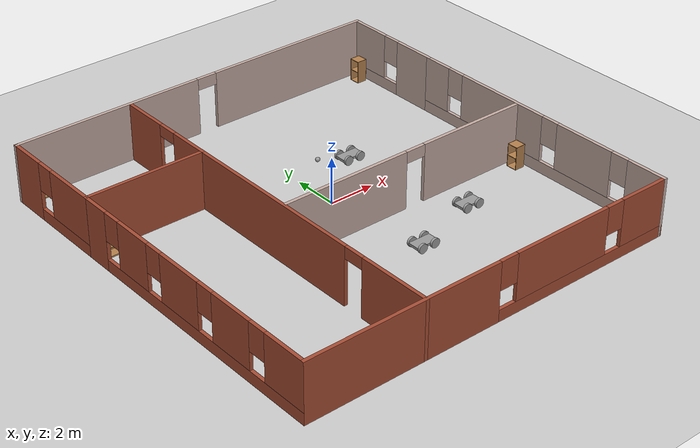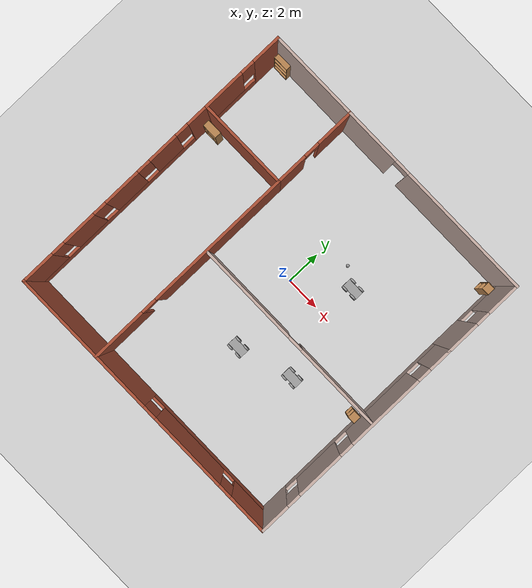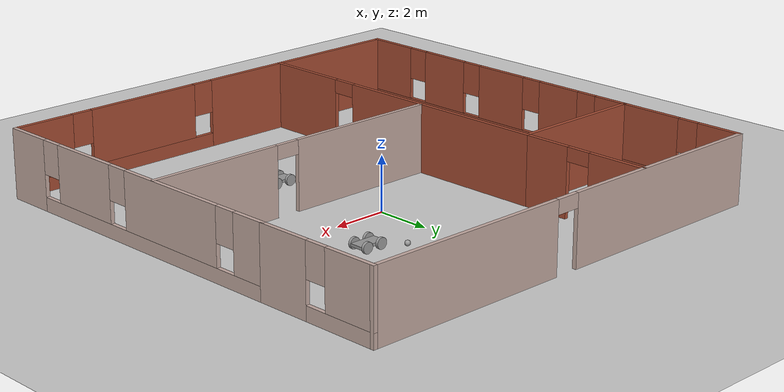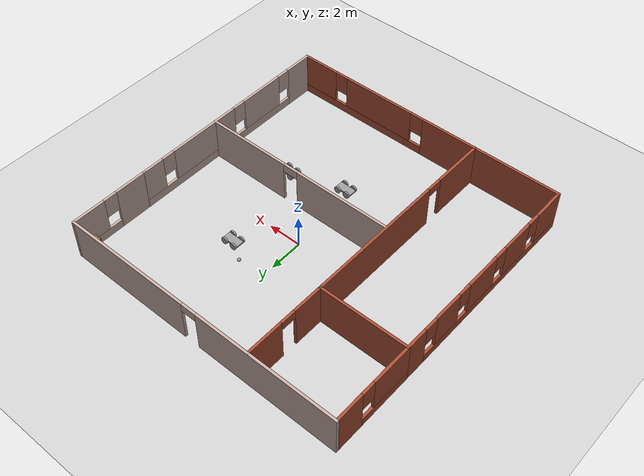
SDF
<sdf version="1.6">
 <world name="default">
  <plugin name="hello" filename="libhello.so"/>
  <light name="sun" type="directional">
   <pose>0 0 10 0 -0 0</pose>
   <diffuse>0.8 0.8 0.8 1</diffuse>
   <specular>0.2 0.2 0.2 1</specular>
   <attenuation>
    <range>1000</range>
    <constant>0.9</constant>
    <linear>0.01</linear>
    <quadratic>0.001</quadratic>
   </attenuation>
   <direction>-0.5 0.1 -0.9</direction>
  </light>
  <model name="ground_plane">
   <static>1</static>
   <link name="link">
    <collision name="collision">
     <geometry><plane><normal>0 0 1</normal><size>100 100</size></plane></geometry>
     <surface>
      <contact><collide_bitmask>65535</collide_bitmask></contact>
      <friction><ode><mu>100</mu><mu2>50</mu2></ode></friction>
     </surface>
    </collision>
    <visual name="visual">
     <cast_shadows>0</cast_shadows>
     <geometry><plane><normal>0 0 1</normal><size>100 100</size></plane></geometry>
     <material>
      <script><uri>file://media/materials/scripts/gazebo.material</uri><name>Gazebo/Grey</name></script>
     </material>
    </visual>
   </link>
  </model>
  <gravity>0 0 -9.8</gravity>
  <magnetic_field>6e-06 2.3e-05 -4.2e-05</magnetic_field>
  <atmosphere type="adiabatic"/>
  <physics name="default_physics" default="0" type="ode">
   <max_step_size>0.001</max_step_size>
   <real_time_factor>1</real_time_factor>
   <real_time_update_rate>1000</real_time_update_rate>
  </physics>
  <scene><ambient>0.4 0.4 0.4 1</ambient><background>0.7 0.7 0.7 1</background><shadows>1</shadows></scene>
  <spherical_coordinates>
   <surface_model>EARTH_WGS84</surface_model>
   <latitude_deg>0</latitude_deg>
   <longitude_deg>0</longitude_deg>
   <elevation>0</elevation>
   <heading_deg>0</heading_deg>
  </spherical_coordinates>
  <model name="buildingone">
   <pose>-0.60257 -0.89389 0 0 -0 0</pose>
   <link name="Wall_71">
    <pose>-8.425 -2.425 0 0 0 -1.5708</pose>
    <visual name="Wall_71_Visual_0">
     <pose>-5.57646 0 1.25 0 -0 0</pose>
     <geometry><box><size>1.34707 0.15 2.5</size></box></geometry>
     <material>
      <script><uri>file://media/materials/scripts/gazebo.material</uri><name>Gazebo/Bricks</name></script>
      <ambient>1 1 1 1</ambient>
     </material>
     <meta><layer>0</layer></meta>
    </visual>
    <collision name="Wall_71_Collision_0">
     <geometry><box><size>1.34707 0.15 2.5</size></box></geometry>
     <pose>-5.57646 0 1.25 0 -0 0</pose>
    </collision>
    <visual name="Wall_71_Visual_1">
     <pose>0.673536 0 0.25 0 -0 0</pose>
     <geometry><box><size>11.1529 0.15 0.5</size></box></geometry>
     <material>
      <script><uri>file://media/materials/scripts/gazebo.material</uri><name>Gazebo/Bricks</name></script>
      <ambient>1 1 1 1</ambient>
     </material>
     <meta><layer>0</layer></meta>
    </visual>
    <collision name="Wall_71_Collision_1">
     <geometry><box><size>11.1529 0.15 0.5</size></box></geometry>
     <pose>0.673536 0 0.25 0 -0 0</pose>
    </collision>
    <visual name="Wall_71_Visual_2">
     <pose>-3.21249 0 1.5 0 -0 0</pose>
     <geometry><box><size>1.78088 0.15 2</size></box></geometry>
     <material>
      <script><uri>file://media/materials/scripts/gazebo.material</uri><name>Gazebo/Bricks</name></script>
      <ambient>1 1 1 1</ambient>
     </material>
     <meta><layer>0</layer></meta>
    </visual>
    <collision name="Wall_71_Collision_2">
     <geometry><box><size>1.78088 0.15 2</size></box></geometry>
     <pose>-3.21249 0 1.5 0 -0 0</pose>
    </collision>
    <visual name="Wall_71_Visual_3">
     <pose>-0.440981 0 1.5 0 -0 0</pose>
     <geometry><box><size>2.16214 0.15 2</size></box></geometry>
     <material>
      <script><uri>file://media/materials/scripts/gazebo.material</uri><name>Gazebo/Bricks</name></script>
      <ambient>1 1 1 1</ambient>
     </material>
     <meta><layer>0</layer></meta>
    </visual>
    <collision name="Wall_71_Collision_3">
     <geometry><box><size>2.16214 0.15 2</size></box></geometry>
     <pose>-0.440981 0 1.5 0 -0 0</pose>
    </collision>
    <visual name="Wall_71_Visual_4">
     <pose>2.44784 0 1.5 0 -0 0</pose>
     <geometry><box><size>2.0155 0.15 2</size></box></geometry>
     <material>
      <script><uri>file://media/materials/scripts/gazebo.material</uri><name>Gazebo/Bricks</name></script>
      <ambient>1 1 1 1</ambient>
     </material>
     <meta><layer>0</layer></meta>
    </visual>
    <collision name="Wall_71_Collision_4">
     <geometry><box><size>2.0155 0.15 2</size></box></geometry>
     <pose>2.44784 0 1.5 0 -0 0</pose>
    </collision>
    <visual name="Wall_71_Visual_5">
     <pose>5.25279 0 1.5 0 -0 0</pose>
     <geometry><box><size>1.99441 0.15 2</size></box></geometry>
     <material>
      <script><uri>file://media/materials/scripts/gazebo.material</uri><name>Gazebo/Bricks</name></script>
      <ambient>1 1 1 1</ambient>
     </material>
     <meta><layer>0</layer></meta>
    </visual>
    <collision name="Wall_71_Collision_5">
     <geometry><box><size>1.99441 0.15 2</size></box></geometry>
     <pose>5.25279 0 1.5 0 -0 0</pose>
    </collision>
    <visual name="Wall_71_Visual_6">
     <pose>-4.50293 0 1.9 0 -0 0</pose>
     <geometry><box><size>0.8 0.15 1.2</size></box></geometry>
     <material>
      <script><uri>file://media/materials/scripts/gazebo.material</uri><name>Gazebo/Bricks</name></script>
      <ambient>1 1 1 1</ambient>
     </material>
     <meta><layer>0</layer></meta>
    </visual>
    <collision name="Wall_71_Collision_6">
     <geometry><box><size>0.8 0.15 1.2</size></box></geometry>
     <pose>-4.50293 0 1.9 0 -0 0</pose>
    </collision>
    <visual name="Wall_71_Visual_7">
     <pose>-1.92205 0 1.9 0 -0 0</pose>
     <geometry><box><size>0.8 0.15 1.2</size></box></geometry>
     <material>
      <script><uri>file://media/materials/scripts/gazebo.material</uri><name>Gazebo/Bricks</name></script>
      <ambient>1 1 1 1</ambient>
     </material>
     <meta><layer>0</layer></meta>
    </visual>
    <collision name="Wall_71_Collision_7">
     <geometry><box><size>0.8 0.15 1.2</size></box></geometry>
     <pose>-1.92205 0 1.9 0 -0 0</pose>
    </collision>
    <visual name="Wall_71_Visual_8">
     <pose>1.04009 0 1.9 0 -0 0</pose>
     <geometry><box><size>0.8 0.15 1.2</size></box></geometry>
     <material>
      <script><uri>file://media/materials/scripts/gazebo.material</uri><name>Gazebo/Bricks</name></script>
      <ambient>1 1 1 1</ambient>
     </material>
     <meta><layer>0</layer></meta>
    </visual>
    <collision name="Wall_71_Collision_8">
     <geometry><box><size>0.8 0.15 1.2</size></box></geometry>
     <pose>1.04009 0 1.9 0 -0 0</pose>
    </collision>
    <visual name="Wall_71_Visual_9">
     <pose>3.85559 0 1.9 0 -0 0</pose>
     <geometry><box><size>0.8 0.15 1.2</size></box></geometry>
     <material>
      <script><uri>file://media/materials/scripts/gazebo.material</uri><name>Gazebo/Bricks</name></script>
      <ambient>1 1 1 1</ambient>
     </material>
     <meta><layer>0</layer></meta>
    </visual>
    <collision name="Wall_71_Collision_9">
     <geometry><box><size>0.8 0.15 1.2</size></box></geometry>
     <pose>3.85559 0 1.9 0 -0 0</pose>
    </collision>
   </link>
   <link name="Wall_72">
    <pose>0 -8.6 0 0 -0 0</pose>
    <visual name="Wall_72_Visual_0">
     <pose>-4.22455 0 1.25 0 -0 0</pose>
     <geometry><box><size>8.55091 0.15 2.5</size></box></geometry>
     <material>
      <script><uri>file://media/materials/scripts/gazebo.material</uri><name>Gazebo/Bricks</name></script>
      <ambient>1 1 1 1</ambient>
     </material>
     <meta><layer>0</layer></meta>
    </visual>
    <collision name="Wall_72_Collision_0">
     <geometry><box><size>8.55091 0.15 2.5</size></box></geometry>
     <pose>-4.22455 0 1.25 0 -0 0</pose>
    </collision>
    <visual name="Wall_72_Visual_1">
     <pose>4.27545 0 0.25 0 -0 0</pose>
     <geometry><box><size>8.44909 0.15 0.5</size></box></geometry>
     <material>
      <script><uri>file://media/materials/scripts/gazebo.material</uri><name>Gazebo/Bricks</name></script>
      <ambient>1 1 1 1</ambient>
     </material>
     <meta><layer>0</layer></meta>
    </visual>
    <collision name="Wall_72_Collision_1">
     <geometry><box><size>8.44909 0.15 0.5</size></box></geometry>
     <pose>4.27545 0 0.25 0 -0 0</pose>
    </collision>
    <visual name="Wall_72_Visual_2">
     <pose>3.10487 0 1.5 0 -0 0</pose>
     <geometry><box><size>4.50793 0.15 2</size></box></geometry>
     <material>
      <script><uri>file://media/materials/scripts/gazebo.material</uri><name>Gazebo/Bricks</name></script>
      <ambient>1 1 1 1</ambient>
     </material>
     <meta><layer>0</layer></meta>
    </visual>
    <collision name="Wall_72_Collision_2">
     <geometry><box><size>4.50793 0.15 2</size></box></geometry>
     <pose>3.10487 0 1.5 0 -0 0</pose>
    </collision>
    <visual name="Wall_72_Visual_3">
     <pose>7.32942 0 1.5 0 -0 0</pose>
     <geometry><box><size>2.34117 0.15 2</size></box></geometry>
     <material>
      <script><uri>file://media/materials/scripts/gazebo.material</uri><name>Gazebo/Bricks</name></script>
      <ambient>1 1 1 1</ambient>
     </material>
     <meta><layer>0</layer></meta>
    </visual>
    <collision name="Wall_72_Collision_3">
     <geometry><box><size>2.34117 0.15 2</size></box></geometry>
     <pose>7.32942 0 1.5 0 -0 0</pose>
    </collision>
    <visual name="Wall_72_Visual_4">
     <pose>0.450905 0 1.9 0 -0 0</pose>
     <geometry><box><size>0.8 0.15 1.2</size></box></geometry>
     <material>
      <script><uri>file://media/materials/scripts/gazebo.material</uri><name>Gazebo/Bricks</name></script>
      <ambient>1 1 1 1</ambient>
     </material>
     <meta><layer>0</layer></meta>
    </visual>
    <collision name="Wall_72_Collision_4">
     <geometry><box><size>0.8 0.15 1.2</size></box></geometry>
     <pose>0.450905 0 1.9 0 -0 0</pose>
    </collision>
    <visual name="Wall_72_Visual_5">
     <pose>5.75883 0 1.9 0 -0 0</pose>
     <geometry><box><size>0.8 0.15 1.2</size></box></geometry>
     <material>
      <script><uri>file://media/materials/scripts/gazebo.material</uri><name>Gazebo/Bricks</name></script>
      <ambient>1 1 1 1</ambient>
     </material>
     <meta><layer>0</layer></meta>
    </visual>
    <collision name="Wall_72_Collision_5">
     <geometry><box><size>0.8 0.15 1.2</size></box></geometry>
     <pose>5.75883 0 1.9 0 -0 0</pose>
    </collision>
   </link>
   <link name="Wall_73">
    <pose>8.425 -2.3 0 0 -0 1.5708</pose>
    <visual name="Wall_73_Visual_0">
     <pose>-5.48571 0 1.25 0 -0 0</pose>
     <geometry><box><size>1.77858 0.15 2.5</size></box></geometry>
     <material>
      <script><uri>file://media/materials/scripts/gazebo.material</uri><name>Gazebo/Grey</name></script>
      <ambient>0.760784 0.662745 0.627451 1</ambient>
     </material>
     <meta><layer>0</layer></meta>
    </visual>
    <collision name="Wall_73_Collision_0">
     <geometry><box><size>1.77858 0.15 2.5</size></box></geometry>
     <pose>-5.48571 0 1.25 0 -0 0</pose>
    </collision>
    <visual name="Wall_73_Visual_1">
     <pose>0.889291 0 0.25 0 -0 0</pose>
     <geometry><box><size>10.9714 0.15 0.5</size></box></geometry>
     <material>
      <script><uri>file://media/materials/scripts/gazebo.material</uri><name>Gazebo/Grey</name></script>
      <ambient>0.760784 0.662745 0.627451 1</ambient>
     </material>
     <meta><layer>0</layer></meta>
    </visual>
    <collision name="Wall_73_Collision_1">
     <geometry><box><size>10.9714 0.15 0.5</size></box></geometry>
     <pose>0.889291 0 0.25 0 -0 0</pose>
    </collision>
    <visual name="Wall_73_Visual_2">
     <pose>-2.41224 0 1.5 0 -0 0</pose>
     <geometry><box><size>2.76835 0.15 2</size></box></geometry>
     <material>
      <script><uri>file://media/materials/scripts/gazebo.material</uri><name>Gazebo/Grey</name></script>
      <ambient>0.760784 0.662745 0.627451 1</ambient>
     </material>
     <meta><layer>0</layer></meta>
    </visual>
    <collision name="Wall_73_Collision_2">
     <geometry><box><size>2.76835 0.15 2</size></box></geometry>
     <pose>-2.41224 0 1.5 0 -0 0</pose>
    </collision>
    <visual name="Wall_73_Visual_3">
     <pose>2.0036 0 1.5 0 -0 0</pose>
     <geometry><box><size>4.46332 0.15 2</size></box></geometry>
     <material>
      <script><uri>file://media/materials/scripts/gazebo.material</uri><name>Gazebo/Grey</name></script>
      <ambient>0.760784 0.662745 0.627451 1</ambient>
     </material>
     <meta><layer>0</layer></meta>
    </visual>
    <collision name="Wall_73_Collision_3">
     <geometry><box><size>4.46332 0.15 2</size></box></geometry>
     <pose>2.0036 0 1.5 0 -0 0</pose>
    </collision>
    <visual name="Wall_73_Visual_4">
     <pose>5.70513 0 1.5 0 -0 0</pose>
     <geometry><box><size>1.33974 0.15 2</size></box></geometry>
     <material>
      <script><uri>file://media/materials/scripts/gazebo.material</uri><name>Gazebo/Grey</name></script>
      <ambient>0.760784 0.662745 0.627451 1</ambient>
     </material>
     <meta><layer>0</layer></meta>
    </visual>
    <collision name="Wall_73_Collision_4">
     <geometry><box><size>1.33974 0.15 2</size></box></geometry>
     <pose>5.70513 0 1.5 0 -0 0</pose>
    </collision>
    <visual name="Wall_73_Visual_5">
     <pose>-4.19642 0 1.9 0 -0 0</pose>
     <geometry><box><size>0.8 0.15 1.2</size></box></geometry>
     <material>
      <script><uri>file://media/materials/scripts/gazebo.material</uri><name>Gazebo/Grey</name></script>
      <ambient>0.760784 0.662745 0.627451 1</ambient>
     </material>
     <meta><layer>0</layer></meta>
    </visual>
    <collision name="Wall_73_Collision_5">
     <geometry><box><size>0.8 0.15 1.2</size></box></geometry>
     <pose>-4.19642 0 1.9 0 -0 0</pose>
    </collision>
    <visual name="Wall_73_Visual_6">
     <pose>-0.628064 0 1.9 0 -0 0</pose>
     <geometry><box><size>0.8 0.15 1.2</size></box></geometry>
     <material>
      <script><uri>file://media/materials/scripts/gazebo.material</uri><name>Gazebo/Grey</name></script>
      <ambient>0.760784 0.662745 0.627451 1</ambient>
     </material>
     <meta><layer>0</layer></meta>
    </visual>
    <collision name="Wall_73_Collision_6">
     <geometry><box><size>0.8 0.15 1.2</size></box></geometry>
     <pose>-0.628064 0 1.9 0 -0 0</pose>
    </collision>
    <visual name="Wall_73_Visual_7">
     <pose>4.63526 0 1.9 0 -0 0</pose>
     <geometry><box><size>0.8 0.15 1.2</size></box></geometry>
     <material>
      <script><uri>file://media/materials/scripts/gazebo.material</uri><name>Gazebo/Grey</name></script>
      <ambient>0.760784 0.662745 0.627451 1</ambient>
     </material>
     <meta><layer>0</layer></meta>
    </visual>
    <collision name="Wall_73_Collision_7">
     <geometry><box><size>0.8 0.15 1.2</size></box></geometry>
     <pose>4.63526 0 1.9 0 -0 0</pose>
    </collision>
   </link>
   <link name="Wall_74">
    <pose>8.425 6.3 0 0 -0 1.5708</pose>
    <visual name="Wall_74_Visual_0">
     <pose>-1.38497 0 1.25 0 -0 0</pose>
     <geometry><box><size>1.98005 0.15 2.5</size></box></geometry>
     <material>
      <script><uri>file://media/materials/scripts/gazebo.material</uri><name>Gazebo/Grey</name></script>
      <ambient>0.760784 0.662745 0.627451 1</ambient>
     </material>
     <meta><layer>0</layer></meta>
    </visual>
    <collision name="Wall_74_Collision_0">
     <geometry><box><size>1.98005 0.15 2.5</size></box></geometry>
     <pose>-1.38497 0 1.25 0 -0 0</pose>
    </collision>
    <visual name="Wall_74_Visual_1">
     <pose>0.990026 0 0.25 0 -0 0</pose>
     <geometry><box><size>2.76995 0.15 0.5</size></box></geometry>
     <material>
      <script><uri>file://media/materials/scripts/gazebo.material</uri><name>Gazebo/Grey</name></script>
      <ambient>0.760784 0.662745 0.627451 1</ambient>
     </material>
     <meta><layer>0</layer></meta>
    </visual>
    <collision name="Wall_74_Collision_1">
     <geometry><box><size>2.76995 0.15 0.5</size></box></geometry>
     <pose>0.990026 0 0.25 0 -0 0</pose>
    </collision>
    <visual name="Wall_74_Visual_2">
     <pose>1.39003 0 1.5 0 -0 0</pose>
     <geometry><box><size>1.96995 0.15 2</size></box></geometry>
     <material>
      <script><uri>file://media/materials/scripts/gazebo.material</uri><name>Gazebo/Grey</name></script>
      <ambient>0.760784 0.662745 0.627451 1</ambient>
     </material>
     <meta><layer>0</layer></meta>
    </visual>
    <collision name="Wall_74_Collision_2">
     <geometry><box><size>1.96995 0.15 2</size></box></geometry>
     <pose>1.39003 0 1.5 0 -0 0</pose>
    </collision>
    <visual name="Wall_74_Visual_3">
     <pose>0.005052 0 1.9 0 -0 0</pose>
     <geometry><box><size>0.8 0.15 1.2</size></box></geometry>
     <material>
      <script><uri>file://media/materials/scripts/gazebo.material</uri><name>Gazebo/Grey</name></script>
      <ambient>0.760784 0.662745 0.627451 1</ambient>
     </material>
     <meta><layer>0</layer></meta>
    </visual>
    <collision name="Wall_74_Collision_3">
     <geometry><box><size>0.8 0.15 1.2</size></box></geometry>
     <pose>0.005052 0 1.9 0 -0 0</pose>
    </collision>
   </link>
   <link name="Wall_75">
    <pose>0 8.6 0 0 -0 3.14159</pose>
    <visual name="Wall_75_Visual_0">
     <pose>-4.65585 0 1.25 0 -0 0</pose>
     <geometry><box><size>7.6883 0.15 2.5</size></box></geometry>
     <material>
      <script><uri>file://media/materials/scripts/gazebo.material</uri><name>Gazebo/Grey</name></script>
      <ambient>0.760784 0.662745 0.627451 1</ambient>
     </material>
     <meta><layer>0</layer></meta>
    </visual>
    <collision name="Wall_75_Collision_0">
     <geometry><box><size>7.6883 0.15 2.5</size></box></geometry>
     <pose>-4.65585 0 1.25 0 -0 0</pose>
    </collision>
    <visual name="Wall_75_Visual_1">
     <pose>4.29415 0 1.25 0 -0 0</pose>
     <geometry><box><size>8.4117 0.15 2.5</size></box></geometry>
     <material>
      <script><uri>file://media/materials/scripts/gazebo.material</uri><name>Gazebo/Grey</name></script>
      <ambient>0.760784 0.662745 0.627451 1</ambient>
     </material>
     <meta><layer>0</layer></meta>
    </visual>
    <collision name="Wall_75_Collision_1">
     <geometry><box><size>8.4117 0.15 2.5</size></box></geometry>
     <pose>4.29415 0 1.25 0 -0 0</pose>
    </collision>
    <visual name="Wall_75_Visual_2">
     <pose>-0.361696 0 2.25 0 -0 0</pose>
     <geometry><box><size>0.9 0.15 0.5</size></box></geometry>
     <material>
      <script><uri>file://media/materials/scripts/gazebo.material</uri><name>Gazebo/Grey</name></script>
      <ambient>0.760784 0.662745 0.627451 1</ambient>
     </material>
     <meta><layer>0</layer></meta>
    </visual>
    <collision name="Wall_75_Collision_2">
     <geometry><box><size>0.9 0.15 0.5</size></box></geometry>
     <pose>-0.361696 0 2.25 0 -0 0</pose>
    </collision>
   </link>
   <link name="Wall_76">
    <pose>-8.425 6.175 0 0 0 -1.5708</pose>
    <visual name="Wall_76_Visual_0">
     <pose>-1.62654 0 1.25 0 -0 0</pose>
     <geometry><box><size>1.74693 0.15 2.5</size></box></geometry>
     <material>
      <script><uri>file://media/materials/scripts/gazebo.material</uri><name>Gazebo/Bricks</name></script>
      <ambient>1 1 1 1</ambient>
     </material>
     <meta><layer>0</layer></meta>
    </visual>
    <collision name="Wall_76_Collision_0">
     <geometry><box><size>1.74693 0.15 2.5</size></box></geometry>
     <pose>-1.62654 0 1.25 0 -0 0</pose>
    </collision>
    <visual name="Wall_76_Visual_1">
     <pose>0.873463 0 0.25 0 -0 0</pose>
     <geometry><box><size>3.25307 0.15 0.5</size></box></geometry>
     <material>
      <script><uri>file://media/materials/scripts/gazebo.material</uri><name>Gazebo/Bricks</name></script>
      <ambient>1 1 1 1</ambient>
     </material>
     <meta><layer>0</layer></meta>
    </visual>
    <collision name="Wall_76_Collision_1">
     <geometry><box><size>3.25307 0.15 0.5</size></box></geometry>
     <pose>0.873463 0 0.25 0 -0 0</pose>
    </collision>
    <visual name="Wall_76_Visual_2">
     <pose>1.27346 0 1.5 0 -0 0</pose>
     <geometry><box><size>2.45307 0.15 2</size></box></geometry>
     <material>
      <script><uri>file://media/materials/scripts/gazebo.material</uri><name>Gazebo/Bricks</name></script>
      <ambient>1 1 1 1</ambient>
     </material>
     <meta><layer>0</layer></meta>
    </visual>
    <collision name="Wall_76_Collision_2">
     <geometry><box><size>2.45307 0.15 2</size></box></geometry>
     <pose>1.27346 0 1.5 0 -0 0</pose>
    </collision>
    <visual name="Wall_76_Visual_3">
     <pose>-0.353074 0 1.9 0 -0 0</pose>
     <geometry><box><size>0.8 0.15 1.2</size></box></geometry>
     <material>
      <script><uri>file://media/materials/scripts/gazebo.material</uri><name>Gazebo/Bricks</name></script>
      <ambient>1 1 1 1</ambient>
     </material>
     <meta><layer>0</layer></meta>
    </visual>
    <collision name="Wall_76_Collision_3">
     <geometry><box><size>0.8 0.15 1.2</size></box></geometry>
     <pose>-0.353074 0 1.9 0 -0 0</pose>
    </collision>
   </link>
   <link name="Wall_77">
    <collision name="Wall_77_Collision">
     <geometry><box><size>5.25 0.15 2.5</size></box></geometry>
     <pose>0 0 1.25 0 -0 0</pose>
    </collision>
    <visual name="Wall_77_Visual">
     <pose>0 0 1.25 0 -0 0</pose>
     <geometry><box><size>5.25 0.15 2.5</size></box></geometry>
     <material>
      <script><uri>file://media/materials/scripts/gazebo.material</uri><name>Gazebo/Bricks</name></script>
      <ambient>1 1 1 1</ambient>
     </material>
     <meta><layer>0</layer></meta>
    </visual>
    <pose>-5.875 3.75 0 0 -0 0</pose>
   </link>
   <link name="Wall_78">
    <pose>-3.325 6.175 0 0 -0 1.5708</pose>
    <visual name="Wall_78_Visual_0">
     <pose>-1.56609 0 1.25 0 -0 0</pose>
     <geometry><box><size>1.86782 0.15 2.5</size></box></geometry>
     <material>
      <script><uri>file://media/materials/scripts/gazebo.material</uri><name>Gazebo/Bricks</name></script>
      <ambient>1 1 1 1</ambient>
     </material>
     <meta><layer>0</layer></meta>
    </visual>
    <collision name="Wall_78_Collision_0">
     <geometry><box><size>1.86782 0.15 2.5</size></box></geometry>
     <pose>-1.56609 0 1.25 0 -0 0</pose>
    </collision>
    <visual name="Wall_78_Visual_1">
     <pose>1.38391 0 1.25 0 -0 0</pose>
     <geometry><box><size>2.23218 0.15 2.5</size></box></geometry>
     <material>
      <script><uri>file://media/materials/scripts/gazebo.material</uri><name>Gazebo/Bricks</name></script>
      <ambient>1 1 1 1</ambient>
     </material>
     <meta><layer>0</layer></meta>
    </visual>
    <collision name="Wall_78_Collision_1">
     <geometry><box><size>2.23218 0.15 2.5</size></box></geometry>
     <pose>1.38391 0 1.25 0 -0 0</pose>
    </collision>
    <visual name="Wall_78_Visual_2">
     <pose>-0.182179 0 2.25 0 -0 0</pose>
     <geometry><box><size>0.9 0.15 0.5</size></box></geometry>
     <material>
      <script><uri>file://media/materials/scripts/gazebo.material</uri><name>Gazebo/Bricks</name></script>
      <ambient>1 1 1 1</ambient>
     </material>
     <meta><layer>0</layer></meta>
    </visual>
    <collision name="Wall_78_Collision_2">
     <geometry><box><size>0.9 0.15 0.5</size></box></geometry>
     <pose>-0.182179 0 2.25 0 -0 0</pose>
    </collision>
   </link>
   <link name="Wall_81">
    <pose>-3.325 -2.425 0 0 0 -1.5708</pose>
    <visual name="Wall_81_Visual_0">
     <pose>-2.05026 0 1.25 0 -0 0</pose>
     <geometry><box><size>8.39947 0.15 2.5</size></box></geometry>
     <material>
      <script><uri>file://media/materials/scripts/gazebo.material</uri><name>Gazebo/Bricks</name></script>
      <ambient>1 1 1 1</ambient>
     </material>
     <meta><layer>0</layer></meta>
    </visual>
    <collision name="Wall_81_Collision_0">
     <geometry><box><size>8.39947 0.15 2.5</size></box></geometry>
     <pose>-2.05026 0 1.25 0 -0 0</pose>
    </collision>
    <visual name="Wall_81_Visual_1">
     <pose>4.64974 0 1.25 0 -0 0</pose>
     <geometry><box><size>3.20053 0.15 2.5</size></box></geometry>
     <material>
      <script><uri>file://media/materials/scripts/gazebo.material</uri><name>Gazebo/Bricks</name></script>
      <ambient>1 1 1 1</ambient>
     </material>
     <meta><layer>0</layer></meta>
    </visual>
    <collision name="Wall_81_Collision_1">
     <geometry><box><size>3.20053 0.15 2.5</size></box></geometry>
     <pose>4.64974 0 1.25 0 -0 0</pose>
    </collision>
    <visual name="Wall_81_Visual_2">
     <pose>2.59947 0 2.25 0 -0 0</pose>
     <geometry><box><size>0.9 0.15 0.5</size></box></geometry>
     <material>
      <script><uri>file://media/materials/scripts/gazebo.material</uri><name>Gazebo/Bricks</name></script>
      <ambient>1 1 1 1</ambient>
     </material>
     <meta><layer>0</layer></meta>
    </visual>
    <collision name="Wall_81_Collision_2">
     <geometry><box><size>0.9 0.15 0.5</size></box></geometry>
     <pose>2.59947 0 2.25 0 -0 0</pose>
    </collision>
   </link>
   <link name="Wall_83">
    <pose>2.59035 -1.15052 0 0 -0 0</pose>
    <visual name="Wall_83_Visual_0">
     <pose>-2.9833 0 1.25 0 -0 0</pose>
     <geometry><box><size>5.7834 0.15 2.5</size></box></geometry>
     <material>
      <script><uri>file://media/materials/scripts/gazebo.material</uri><name>Gazebo/Grey</name></script>
      <ambient>0.760784 0.662745 0.627451 1</ambient>
     </material>
     <meta><layer>0</layer></meta>
    </visual>
    <collision name="Wall_83_Collision_0">
     <geometry><box><size>5.7834 0.15 2.5</size></box></geometry>
     <pose>-2.9833 0 1.25 0 -0 0</pose>
    </collision>
    <visual name="Wall_83_Visual_1">
     <pose>3.3417 0 1.25 0 -0 0</pose>
     <geometry><box><size>5.0666 0.15 2.5</size></box></geometry>
     <material>
      <script><uri>file://media/materials/scripts/gazebo.material</uri><name>Gazebo/Grey</name></script>
      <ambient>0.760784 0.662745 0.627451 1</ambient>
     </material>
     <meta><layer>0</layer></meta>
    </visual>
    <collision name="Wall_83_Collision_1">
     <geometry><box><size>5.0666 0.15 2.5</size></box></geometry>
     <pose>3.3417 0 1.25 0 -0 0</pose>
    </collision>
    <visual name="Wall_83_Visual_2">
     <pose>0.358404 0 2.25 0 -0 0</pose>
     <geometry><box><size>0.9 0.15 0.5</size></box></geometry>
     <material>
      <script><uri>file://media/materials/scripts/gazebo.material</uri><name>Gazebo/Grey</name></script>
      <ambient>0.760784 0.662745 0.627451 1</ambient>
     </material>
     <meta><layer>0</layer></meta>
    </visual>
    <collision name="Wall_83_Collision_2">
     <geometry><box><size>0.9 0.15 0.5</size></box></geometry>
     <pose>0.358404 0 2.25 0 -0 0</pose>
    </collision>
   </link>
   <static>1</static>
  </model>
  <model name="cabinet">
   <static>1</static>
   <link name="cabinet_bottom_plate">
    <inertial>
     <pose>0 0 -1 0 -0 0</pose>
     <inertia><ixx>2.05</ixx><ixy>0</ixy><ixz>0</ixz><iyy>2.05</iyy><iyz>0</iyz><izz>2.05</izz></inertia>
     <mass>25</mass>
    </inertial>
    <collision name="cabinet_bottom_plate_geom">
     <pose>0 0 0.01 0 -0 0</pose>
     <geometry><box><size>0.45 0.45 0.02</size></box></geometry>
    </collision>
    <visual name="cabinet_bottom_plate_geom_visual">
     <pose>0 0 0.01 0 -0 0</pose>
     <geometry><box><size>0.45 0.45 0.02</size></box></geometry>
     <material>
      <script><uri>file://media/materials/scripts/gazebo.material</uri><name>Gazebo/Wood</name></script>
     </material>
    </visual>
    <collision name="cabinet_bottom_plate_geom_cabinet_back_plate">
     <pose>0.235 0 0.51 0 -0 0</pose>
     <geometry><box><size>0.02 0.45 1.02</size></box></geometry>
    </collision>
    <visual name="cabinet_bottom_plate_geom_cabinet_back_plate_visual">
     <pose>0.235 0 0.51 0 -0 0</pose>
     <geometry><box><size>0.02 0.45 1.02</size></box></geometry>
     <material>
      <script><uri>file://media/materials/scripts/gazebo.material</uri><name>Gazebo/Wood</name></script>
     </material>
    </visual>
    <collision name="cabinet_bottom_plate_geom_cabinet_left_plate">
     <pose>0 0.235 0.51 0 -0 0</pose>
     <geometry><box><size>0.45 0.02 1.02</size></box></geometry>
    </collision>
    <visual name="cabinet_bottom_plate_geom_cabinet_left_plate_visual">
     <pose>0 0.235 0.51 0 -0 0</pose>
     <geometry><box><size>0.45 0.02 1.02</size></box></geometry>
     <material>
      <script><uri>file://media/materials/scripts/gazebo.material</uri><name>Gazebo/Wood</name></script>
     </material>
    </visual>
    <collision name="cabinet_bottom_plate_geom_cabinet_middle_plate">
     <pose>0 0 0.51 0 -0 0</pose>
     <geometry><box><size>0.45 0.45 0.02</size></box></geometry>
    </collision>
    <visual name="cabinet_bottom_plate_geom_cabinet_middle_plate_visual">
     <pose>0 0 0.51 0 -0 0</pose>
     <geometry><box><size>0.45 0.45 0.02</size></box></geometry>
     <material>
      <script><uri>file://media/materials/scripts/gazebo.material</uri><name>Gazebo/Wood</name></script>
     </material>
    </visual>
    <collision name="cabinet_bottom_plate_geom_cabinet_right_plate">
     <pose>0 -0.235 0.51 0 -0 0</pose>
     <geometry><box><size>0.45 0.02 1.02</size></box></geometry>
    </collision>
    <visual name="cabinet_bottom_plate_geom_cabinet_right_plate_visual">
     <pose>0 -0.235 0.51 0 -0 0</pose>
     <geometry><box><size>0.45 0.02 1.02</size></box></geometry>
     <material>
      <script><uri>file://media/materials/scripts/gazebo.material</uri><name>Gazebo/Wood</name></script>
     </material>
    </visual>
    <collision name="cabinet_bottom_plate_geom_cabinet_top_plate">
     <pose>0 0 1.01 0 -0 0</pose>
     <geometry><box><size>0.45 0.45 0.02</size></box></geometry>
    </collision>
    <visual name="cabinet_bottom_plate_geom_cabinet_top_plate_visual">
     <pose>0 0 1.01 0 -0 0</pose>
     <geometry><box><size>0.45 0.45 0.02</size></box></geometry>
     <material>
      <script><uri>file://media/materials/scripts/gazebo.material</uri><name>Gazebo/Wood</name></script>
     </material>
    </visual>
   </link>
   <pose>7.38503 7.08593 0 0 -0 0</pose>
  </model>
  <model name="cabinet_0">
   <static>1</static>
   <link name="cabinet_bottom_plate">
    <inertial>
     <pose>0 0 -1 0 -0 0</pose>
     <inertia><ixx>2.05</ixx><ixy>0</ixy><ixz>0</ixz><iyy>2.05</iyy><iyz>0</iyz><izz>2.05</izz></inertia>
     <mass>25</mass>
    </inertial>
    <collision name="cabinet_bottom_plate_geom">
     <pose>0 0 0.01 0 -0 0</pose>
     <geometry><box><size>0.45 0.45 0.02</size></box></geometry>
    </collision>
    <visual name="cabinet_bottom_plate_geom_visual">
     <pose>0 0 0.01 0 -0 0</pose>
     <geometry><box><size>0.45 0.45 0.02</size></box></geometry>
     <material>
      <script><uri>file://media/materials/scripts/gazebo.material</uri><name>Gazebo/Wood</name></script>
     </material>
    </visual>
    <collision name="cabinet_bottom_plate_geom_cabinet_back_plate">
     <pose>0.235 0 0.51 0 -0 0</pose>
     <geometry><box><size>0.02 0.45 1.02</size></box></geometry>
    </collision>
    <visual name="cabinet_bottom_plate_geom_cabinet_back_plate_visual">
     <pose>0.235 0 0.51 0 -0 0</pose>
     <geometry><box><size>0.02 0.45 1.02</size></box></geometry>
     <material>
      <script><uri>file://media/materials/scripts/gazebo.material</uri><name>Gazebo/Wood</name></script>
     </material>
    </visual>
    <collision name="cabinet_bottom_plate_geom_cabinet_left_plate">
     <pose>0 0.235 0.51 0 -0 0</pose>
     <geometry><box><size>0.45 0.02 1.02</size></box></geometry>
    </collision>
    <visual name="cabinet_bottom_plate_geom_cabinet_left_plate_visual">
     <pose>0 0.235 0.51 0 -0 0</pose>
     <geometry><box><size>0.45 0.02 1.02</size></box></geometry>
     <material>
      <script><uri>file://media/materials/scripts/gazebo.material</uri><name>Gazebo/Wood</name></script>
     </material>
    </visual>
    <collision name="cabinet_bottom_plate_geom_cabinet_middle_plate">
     <pose>0 0 0.51 0 -0 0</pose>
     <geometry><box><size>0.45 0.45 0.02</size></box></geometry>
    </collision>
    <visual name="cabinet_bottom_plate_geom_cabinet_middle_plate_visual">
     <pose>0 0 0.51 0 -0 0</pose>
     <geometry><box><size>0.45 0.45 0.02</size></box></geometry>
     <material>
      <script><uri>file://media/materials/scripts/gazebo.material</uri><name>Gazebo/Wood</name></script>
     </material>
    </visual>
    <collision name="cabinet_bottom_plate_geom_cabinet_right_plate">
     <pose>0 -0.235 0.51 0 -0 0</pose>
     <geometry><box><size>0.45 0.02 1.02</size></box></geometry>
    </collision>
    <visual name="cabinet_bottom_plate_geom_cabinet_right_plate_visual">
     <pose>0 -0.235 0.51 0 -0 0</pose>
     <geometry><box><size>0.45 0.02 1.02</size></box></geometry>
     <material>
      <script><uri>file://media/materials/scripts/gazebo.material</uri><name>Gazebo/Wood</name></script>
     </material>
    </visual>
    <collision name="cabinet_bottom_plate_geom_cabinet_top_plate">
     <pose>0 0 1.01 0 -0 0</pose>
     <geometry><box><size>0.45 0.45 0.02</size></box></geometry>
    </collision>
    <visual name="cabinet_bottom_plate_geom_cabinet_top_plate_visual">
     <pose>0 0 1.01 0 -0 0</pose>
     <geometry><box><size>0.45 0.45 0.02</size></box></geometry>
     <material>
      <script><uri>file://media/materials/scripts/gazebo.material</uri><name>Gazebo/Wood</name></script>
     </material>
    </visual>
   </link>
   <pose>7.37126 -2.53429 0 0 -0 0</pose>
  </model>
  <model name="bookshelf">
   <static>1</static>
   <link name="link">
    <inertial><mass>1</mass></inertial>
    <collision name="back">
     <pose>0 0.005 0.6 0 -0 0</pose>
     <geometry><box><size>0.9 0.01 1.2</size></box></geometry>
    </collision>
    <visual name="visual1">
     <pose>0 0.005 0.6 0 -0 0</pose>
     <geometry><box><size>0.9 0.01 1.2</size></box></geometry>
     <material>
      <script><uri>file://media/materials/scripts/gazebo.material</uri><name>Gazebo/Wood</name></script>
     </material>
    </visual>
    <collision name="left_side">
     <pose>0.45 -0.195 0.6 0 -0 0</pose>
     <geometry><box><size>0.02 0.4 1.2</size></box></geometry>
    </collision>
    <visual name="visual2">
     <pose>0.45 -0.195 0.6 0 -0 0</pose>
     <geometry><box><size>0.02 0.4 1.2</size></box></geometry>
     <material>
      <script><uri>file://media/materials/scripts/gazebo.material</uri><name>Gazebo/Wood</name></script>
     </material>
    </visual>
    <collision name="right_side">
     <pose>-0.45 -0.195 0.6 0 -0 0</pose>
     <geometry><box><size>0.02 0.4 1.2</size></box></geometry>
    </collision>
    <visual name="visual3">
     <pose>-0.45 -0.195 0.6 0 -0 0</pose>
     <geometry><box><size>0.02 0.4 1.2</size></box></geometry>
     <material>
      <script><uri>file://media/materials/scripts/gazebo.material</uri><name>Gazebo/Wood</name></script>
     </material>
    </visual>
    <collision name="bottom">
     <pose>0 -0.195 0.03 0 -0 0</pose>
     <geometry><box><size>0.88 0.4 0.06</size></box></geometry>
    </collision>
    <visual name="visual4">
     <pose>0 -0.195 0.03 0 -0 0</pose>
     <geometry><box><size>0.88 0.4 0.06</size></box></geometry>
     <material>
      <script><uri>file://media/materials/scripts/gazebo.material</uri><name>Gazebo/Wood</name></script>
     </material>
    </visual>
    <collision name="top">
     <pose>0 -0.195 1.19 0 -0 0</pose>
     <geometry><box><size>0.88 0.4 0.02</size></box></geometry>
    </collision>
    <visual name="visual5">
     <pose>0 -0.195 1.19 0 -0 0</pose>
     <geometry><box><size>0.88 0.4 0.02</size></box></geometry>
     <material>
      <script><uri>file://media/materials/scripts/gazebo.material</uri><name>Gazebo/Wood</name></script>
     </material>
    </visual>
    <collision name="low_shelf">
     <pose>0 -0.195 0.43 0 -0 0</pose>
     <geometry><box><size>0.88 0.4 0.02</size></box></geometry>
    </collision>
    <visual name="visual6">
     <pose>0 -0.195 0.43 0 -0 0</pose>
     <geometry><box><size>0.88 0.4 0.02</size></box></geometry>
     <material>
      <script><uri>file://media/materials/scripts/gazebo.material</uri><name>Gazebo/Wood</name></script>
     </material>
    </visual>
    <collision name="high_shelf">
     <pose>0 -0.195 0.8 0 -0 0</pose>
     <geometry><box><size>0.88 0.4 0.02</size></box></geometry>
    </collision>
    <visual name="visual7">
     <pose>0 -0.195 0.8 0 -0 0</pose>
     <geometry><box><size>0.88 0.4 0.02</size></box></geometry>
     <material>
      <script><uri>file://media/materials/scripts/gazebo.material</uri><name>Gazebo/Wood</name></script>
     </material>
    </visual>
   </link>
   <pose>-8.43868 2.65047 0 0 -0 0</pose>
  </model>
  <model name="bookshelf_0">
   <static>1</static>
   <link name="link">
    <inertial><mass>1</mass></inertial>
    <collision name="back">
     <pose>0 0.005 0.6 0 -0 0</pose>
     <geometry><box><size>0.9 0.01 1.2</size></box></geometry>
    </collision>
    <visual name="visual1">
     <pose>0 0.005 0.6 0 -0 0</pose>
     <geometry><box><size>0.9 0.01 1.2</size></box></geometry>
     <material>
      <script><uri>file://media/materials/scripts/gazebo.material</uri><name>Gazebo/Wood</name></script>
     </material>
    </visual>
    <collision name="left_side">
     <pose>0.45 -0.195 0.6 0 -0 0</pose>
     <geometry><box><size>0.02 0.4 1.2</size></box></geometry>
    </collision>
    <visual name="visual2">
     <pose>0.45 -0.195 0.6 0 -0 0</pose>
     <geometry><box><size>0.02 0.4 1.2</size></box></geometry>
     <material>
      <script><uri>file://media/materials/scripts/gazebo.material</uri><name>Gazebo/Wood</name></script>
     </material>
    </visual>
    <collision name="right_side">
     <pose>-0.45 -0.195 0.6 0 -0 0</pose>
     <geometry><box><size>0.02 0.4 1.2</size></box></geometry>
    </collision>
    <visual name="visual3">
     <pose>-0.45 -0.195 0.6 0 -0 0</pose>
     <geometry><box><size>0.02 0.4 1.2</size></box></geometry>
     <material>
      <script><uri>file://media/materials/scripts/gazebo.material</uri><name>Gazebo/Wood</name></script>
     </material>
    </visual>
    <collision name="bottom">
     <pose>0 -0.195 0.03 0 -0 0</pose>
     <geometry><box><size>0.88 0.4 0.06</size></box></geometry>
    </collision>
    <visual name="visual4">
     <pose>0 -0.195 0.03 0 -0 0</pose>
     <geometry><box><size>0.88 0.4 0.06</size></box></geometry>
     <material>
      <script><uri>file://media/materials/scripts/gazebo.material</uri><name>Gazebo/Wood</name></script>
     </material>
    </visual>
    <collision name="top">
     <pose>0 -0.195 1.19 0 -0 0</pose>
     <geometry><box><size>0.88 0.4 0.02</size></box></geometry>
    </collision>
    <visual name="visual5">
     <pose>0 -0.195 1.19 0 -0 0</pose>
     <geometry><box><size>0.88 0.4 0.02</size></box></geometry>
     <material>
      <script><uri>file://media/materials/scripts/gazebo.material</uri><name>Gazebo/Wood</name></script>
     </material>
    </visual>
    <collision name="low_shelf">
     <pose>0 -0.195 0.43 0 -0 0</pose>
     <geometry><box><size>0.88 0.4 0.02</size></box></geometry>
    </collision>
    <visual name="visual6">
     <pose>0 -0.195 0.43 0 -0 0</pose>
     <geometry><box><size>0.88 0.4 0.02</size></box></geometry>
     <material>
      <script><uri>file://media/materials/scripts/gazebo.material</uri><name>Gazebo/Wood</name></script>
     </material>
    </visual>
    <collision name="high_shelf">
     <pose>0 -0.195 0.8 0 -0 0</pose>
     <geometry><box><size>0.88 0.4 0.02</size></box></geometry>
    </collision>
    <visual name="visual7">
     <pose>0 -0.195 0.8 0 -0 0</pose>
     <geometry><box><size>0.88 0.4 0.02</size></box></geometry>
     <material>
      <script><uri>file://media/materials/scripts/gazebo.material</uri><name>Gazebo/Wood</name></script>
     </material>
    </visual>
   </link>
   <pose>-8.431 7.72676 0 0 -0 0</pose>
  </model>
  <model name="robot1">
   <link name="link_0">
    <inertial>
     <mass>1</mass>
     <inertia>
      <ixx>0.166667</ixx>
      <ixy>0</ixy>
      <ixz>0</ixz>
      <iyy>0.166667</iyy>
      <iyz>0</iyz>
      <izz>0.166667</izz>
     </inertia>
    </inertial>
    <visual name="visual">
     <geometry><box><size>1 0.5 0.1</size></box></geometry>
     <material>
      <lighting>1</lighting>
      <script><uri>file://media/materials/scripts/gazebo.material</uri><name>Gazebo/Grey</name></script>
      <shader type="pixel"><normal_map>__default__</normal_map></shader>
      <ambient>0.3 0.3 0.3 1</ambient>
      <diffuse>0.7 0.7 0.7 1</diffuse>
      <specular>0.01 0.01 0.01 1</specular>
      <emissive>0 0 0 1</emissive>
     </material>
    </visual>
    <collision name="collision">
     <geometry><box><size>1 0.5 0.1</size></box></geometry>
     <surface>
      <friction>
       <ode><mu>1</mu><mu2>1</mu2><fdir1>0 0 0</fdir1><slip1>0</slip1><slip2>0</slip2></ode>
       <torsional>
        <coefficient>1</coefficient>
        <patch_radius>0</patch_radius>
        <surface_radius>0</surface_radius>
        <use_patch_radius>1</use_patch_radius>
        <ode><slip>0</slip></ode>
       </torsional>
      </friction>
      <bounce><restitution_coefficient>0</restitution_coefficient><threshold>1e+06</threshold></bounce>
      <contact>
       <collide_without_contact>0</collide_without_contact>
       <collide_without_contact_bitmask>1</collide_without_contact_bitmask>
       <collide_bitmask>1</collide_bitmask>
       <ode>
        <soft_cfm>0</soft_cfm>
        <soft_erp>0.2</soft_erp>
        <kp>1e+13</kp>
        <kd>1</kd>
        <max_vel>0.01</max_vel>
        <min_depth>0</min_depth>
       </ode>
       <bullet>
        <split_impulse>1</split_impulse>
        <split_impulse_penetration_threshold>-0.01</split_impulse_penetration_threshold>
        <soft_cfm>0</soft_cfm>
        <soft_erp>0.2</soft_erp>
        <kp>1e+13</kp>
        <kd>1</kd>
       </bullet>
      </contact>
     </surface>
    </collision>
   </link>
   <link name="link_1">
    <pose>-0.3 -0.300019 0 1.5707 -0 0</pose>
    <inertial>
     <mass>1</mass>
     <inertia><ixx>0.145833</ixx><ixy>0</ixy><ixz>0</ixz><iyy>0.145833</iyy><iyz>0</iyz><izz>0.125</izz></inertia>
    </inertial>
    <visual name="visual">
     <geometry><cylinder><radius>0.2</radius><length>0.1</length></cylinder></geometry>
     <material>
      <lighting>1</lighting>
      <script><uri>file://media/materials/scripts/gazebo.material</uri><name>Gazebo/Grey</name></script>
      <shader type="pixel"><normal_map>__default__</normal_map></shader>
      <ambient>0.3 0.3 0.3 1</ambient>
      <diffuse>0.7 0.7 0.7 1</diffuse>
      <specular>0.01 0.01 0.01 1</specular>
      <emissive>0 0 0 1</emissive>
     </material>
    </visual>
    <collision name="collision">
     <geometry><cylinder><radius>0.2</radius><length>0.1</length></cylinder></geometry>
     <surface>
      <friction>
       <ode><mu>1</mu><mu2>1</mu2><fdir1>0 0 0</fdir1><slip1>0</slip1><slip2>0</slip2></ode>
       <torsional>
        <coefficient>1</coefficient>
        <patch_radius>0</patch_radius>
        <surface_radius>0</surface_radius>
        <use_patch_radius>1</use_patch_radius>
        <ode><slip>0</slip></ode>
       </torsional>
      </friction>
      <bounce><restitution_coefficient>0</restitution_coefficient><threshold>1e+06</threshold></bounce>
      <contact>
       <collide_without_contact>0</collide_without_contact>
       <collide_without_contact_bitmask>1</collide_without_contact_bitmask>
       <collide_bitmask>1</collide_bitmask>
       <ode>
        <soft_cfm>0</soft_cfm>
        <soft_erp>0.2</soft_erp>
        <kp>1e+13</kp>
        <kd>1</kd>
        <max_vel>0.01</max_vel>
        <min_depth>0</min_depth>
       </ode>
       <bullet>
        <split_impulse>1</split_impulse>
        <split_impulse_penetration_threshold>-0.01</split_impulse_penetration_threshold>
        <soft_cfm>0</soft_cfm>
        <soft_erp>0.2</soft_erp>
        <kp>1e+13</kp>
        <kd>1</kd>
       </bullet>
      </contact>
     </surface>
    </collision>
   </link>
   <link name="link_1_clone">
    <pose>-0.3 0.300019 0 1.5707 -0 0</pose>
    <inertial>
     <mass>1</mass>
     <inertia><ixx>0.145833</ixx><ixy>0</ixy><ixz>0</ixz><iyy>0.145833</iyy><iyz>0</iyz><izz>0.125</izz></inertia>
    </inertial>
    <visual name="visual">
     <geometry><cylinder><radius>0.2</radius><length>0.1</length></cylinder></geometry>
     <material>
      <lighting>1</lighting>
      <script><uri>file://media/materials/scripts/gazebo.material</uri><name>Gazebo/Grey</name></script>
      <shader type="pixel"><normal_map>__default__</normal_map></shader>
      <ambient>0.3 0.3 0.3 1</ambient>
      <diffuse>0.7 0.7 0.7 1</diffuse>
      <specular>0.01 0.01 0.01 1</specular>
      <emissive>0 0 0 1</emissive>
     </material>
    </visual>
    <collision name="collision">
     <geometry><cylinder><radius>0.2</radius><length>0.1</length></cylinder></geometry>
     <surface>
      <friction>
       <ode><mu>1</mu><mu2>1</mu2><fdir1>0 0 0</fdir1><slip1>0</slip1><slip2>0</slip2></ode>
       <torsional>
        <coefficient>1</coefficient>
        <patch_radius>0</patch_radius>
        <surface_radius>0</surface_radius>
        <use_patch_radius>1</use_patch_radius>
        <ode><slip>0</slip></ode>
       </torsional>
      </friction>
      <bounce><restitution_coefficient>0</restitution_coefficient><threshold>1e+06</threshold></bounce>
      <contact>
       <collide_without_contact>0</collide_without_contact>
       <collide_without_contact_bitmask>1</collide_without_contact_bitmask>
       <collide_bitmask>1</collide_bitmask>
       <ode>
        <soft_cfm>0</soft_cfm>
        <soft_erp>0.2</soft_erp>
        <kp>1e+13</kp>
        <kd>1</kd>
        <max_vel>0.01</max_vel>
        <min_depth>0</min_depth>
       </ode>
       <bullet>
        <split_impulse>1</split_impulse>
        <split_impulse_penetration_threshold>-0.01</split_impulse_penetration_threshold>
        <soft_cfm>0</soft_cfm>
        <soft_erp>0.2</soft_erp>
        <kp>1e+13</kp>
        <kd>1</kd>
       </bullet>
      </contact>
     </surface>
    </collision>
   </link>
   <link name="link_1_clone_0">
    <pose>0.3 -0.300019 0 1.5707 -0 0</pose>
    <inertial>
     <mass>1</mass>
     <inertia><ixx>0.145833</ixx><ixy>0</ixy><ixz>0</ixz><iyy>0.145833</iyy><iyz>0</iyz><izz>0.125</izz></inertia>
    </inertial>
    <visual name="visual">
     <geometry><cylinder><radius>0.2</radius><length>0.1</length></cylinder></geometry>
     <material>
      <lighting>1</lighting>
      <script><uri>file://media/materials/scripts/gazebo.material</uri><name>Gazebo/Grey</name></script>
      <shader type="pixel"><normal_map>__default__</normal_map></shader>
      <ambient>0.3 0.3 0.3 1</ambient>
      <diffuse>0.7 0.7 0.7 1</diffuse>
      <specular>0.01 0.01 0.01 1</specular>
      <emissive>0 0 0 1</emissive>
     </material>
    </visual>
    <collision name="collision">
     <geometry><cylinder><radius>0.2</radius><length>0.1</length></cylinder></geometry>
     <surface>
      <friction>
       <ode><mu>1</mu><mu2>1</mu2><fdir1>0 0 0</fdir1><slip1>0</slip1><slip2>0</slip2></ode>
       <torsional>
        <coefficient>1</coefficient>
        <patch_radius>0</patch_radius>
        <surface_radius>0</surface_radius>
        <use_patch_radius>1</use_patch_radius>
        <ode><slip>0</slip></ode>
       </torsional>
      </friction>
      <bounce><restitution_coefficient>0</restitution_coefficient><threshold>1e+06</threshold></bounce>
      <contact>
       <collide_without_contact>0</collide_without_contact>
       <collide_without_contact_bitmask>1</collide_without_contact_bitmask>
       <collide_bitmask>1</collide_bitmask>
       <ode>
        <soft_cfm>0</soft_cfm>
        <soft_erp>0.2</soft_erp>
        <kp>1e+13</kp>
        <kd>1</kd>
        <max_vel>0.01</max_vel>
        <min_depth>0</min_depth>
       </ode>
       <bullet>
        <split_impulse>1</split_impulse>
        <split_impulse_penetration_threshold>-0.01</split_impulse_penetration_threshold>
        <soft_cfm>0</soft_cfm>
        <soft_erp>0.2</soft_erp>
        <kp>1e+13</kp>
        <kd>1</kd>
       </bullet>
      </contact>
     </surface>
    </collision>
   </link>
   <link name="link_1_clone_1">
    <pose>0.3 0.300019 0 1.5707 -0 0</pose>
    <inertial>
     <mass>1</mass>
     <inertia><ixx>0.145833</ixx><ixy>0</ixy><ixz>0</ixz><iyy>0.145833</iyy><iyz>0</iyz><izz>0.125</izz></inertia>
    </inertial>
    <visual name="visual">
     <geometry><cylinder><radius>0.2</radius><length>0.1</length></cylinder></geometry>
     <material>
      <lighting>1</lighting>
      <script><uri>file://media/materials/scripts/gazebo.material</uri><name>Gazebo/Grey</name></script>
      <shader type="pixel"><normal_map>__default__</normal_map></shader>
      <ambient>0.3 0.3 0.3 1</ambient>
      <diffuse>0.7 0.7 0.7 1</diffuse>
      <specular>0.01 0.01 0.01 1</specular>
      <emissive>0 0 0 1</emissive>
     </material>
    </visual>
    <collision name="collision">
     <geometry><cylinder><radius>0.2</radius><length>0.1</length></cylinder></geometry>
     <surface>
      <friction>
       <ode><mu>1</mu><mu2>1</mu2><fdir1>0 0 0</fdir1><slip1>0</slip1><slip2>0</slip2></ode>
       <torsional>
        <coefficient>1</coefficient>
        <patch_radius>0</patch_radius>
        <surface_radius>0</surface_radius>
        <use_patch_radius>1</use_patch_radius>
        <ode><slip>0</slip></ode>
       </torsional>
      </friction>
      <bounce><restitution_coefficient>0</restitution_coefficient><threshold>1e+06</threshold></bounce>
      <contact>
       <collide_without_contact>0</collide_without_contact>
       <collide_without_contact_bitmask>1</collide_without_contact_bitmask>
       <collide_bitmask>1</collide_bitmask>
       <ode>
        <soft_cfm>0</soft_cfm>
        <soft_erp>0.2</soft_erp>
        <kp>1e+13</kp>
        <kd>1</kd>
        <max_vel>0.01</max_vel>
        <min_depth>0</min_depth>
       </ode>
       <bullet>
        <split_impulse>1</split_impulse>
        <split_impulse_penetration_threshold>-0.01</split_impulse_penetration_threshold>
        <soft_cfm>0</soft_cfm>
        <soft_erp>0.2</soft_erp>
        <kp>1e+13</kp>
        <kd>1</kd>
       </bullet>
      </contact>
     </surface>
    </collision>
   </link>
   <joint name="link_0_JOINT_1" type="revolute">
    <parent>link_0</parent>
    <child>link_1_clone</child>
    <axis>
     <xyz>0 0 1</xyz>
     <use_parent_model_frame>0</use_parent_model_frame>
     <limit>
      <lower>-1.79769e+308</lower>
      <upper>1.79769e+308</upper>
      <effort>-1</effort>
      <velocity>-1</velocity>
     </limit>
     <dynamics>
      <spring_reference>0</spring_reference>
      <spring_stiffness>0</spring_stiffness>
      <damping>0</damping>
     </dynamics>
    </axis>
    <physics>
     <ode><limit><cfm>0</cfm><erp>0.2</erp></limit><suspension><cfm>0</cfm><erp>0.2</erp></suspension></ode>
    </physics>
   </joint>
   <joint name="link_0_JOINT_2" type="revolute">
    <parent>link_0</parent>
    <child>link_1</child>
    <axis>
     <xyz>0 0 1</xyz>
     <use_parent_model_frame>0</use_parent_model_frame>
     <limit>
      <lower>-1.79769e+308</lower>
      <upper>1.79769e+308</upper>
      <effort>-1</effort>
      <velocity>-1</velocity>
     </limit>
     <dynamics>
      <spring_reference>0</spring_reference>
      <spring_stiffness>0</spring_stiffness>
      <damping>0</damping>
     </dynamics>
    </axis>
    <physics>
     <ode><limit><cfm>0</cfm><erp>0.2</erp></limit><suspension><cfm>0</cfm><erp>0.2</erp></suspension></ode>
    </physics>
   </joint>
   <joint name="link_0_JOINT_3" type="revolute">
    <parent>link_0</parent>
    <child>link_1_clone_1</child>
    <axis>
     <xyz>0 0 1</xyz>
     <use_parent_model_frame>0</use_parent_model_frame>
     <limit>
      <lower>-1.79769e+308</lower>
      <upper>1.79769e+308</upper>
      <effort>-1</effort>
      <velocity>-1</velocity>
     </limit>
     <dynamics>
      <spring_reference>0</spring_reference>
      <spring_stiffness>0</spring_stiffness>
      <damping>0</damping>
     </dynamics>
    </axis>
    <physics>
     <ode><limit><cfm>0</cfm><erp>0.2</erp></limit><suspension><cfm>0</cfm><erp>0.2</erp></suspension></ode>
    </physics>
   </joint>
   <joint name="link_0_JOINT_4" type="revolute">
    <parent>link_0</parent>
    <child>link_1_clone_0</child>
    <axis>
     <xyz>0 0 1</xyz>
     <use_parent_model_frame>0</use_parent_model_frame>
     <limit>
      <lower>-1.79769e+308</lower>
      <upper>1.79769e+308</upper>
      <effort>-1</effort>
      <velocity>-1</velocity>
     </limit>
     <dynamics>
      <spring_reference>0</spring_reference>
      <spring_stiffness>0</spring_stiffness>
      <damping>0</damping>
     </dynamics>
    </axis>
    <physics>
     <ode><limit><cfm>0</cfm><erp>0.2</erp></limit><suspension><cfm>0</cfm><erp>0.2</erp></suspension></ode>
    </physics>
   </joint>
   <static>0</static>
   <pose>3.81405 -3.51746 0.200005 0 0 -0.013909</pose>
  </model>
  <model name="robot1_0">
   <link name="link_0">
    <inertial>
     <mass>1</mass>
     <inertia>
      <ixx>0.166667</ixx>
      <ixy>0</ixy>
      <ixz>0</ixz>
      <iyy>0.166667</iyy>
      <iyz>0</iyz>
      <izz>0.166667</izz>
     </inertia>
    </inertial>
    <visual name="visual">
     <geometry><box><size>1 0.5 0.1</size></box></geometry>
     <material>
      <lighting>1</lighting>
      <script><uri>file://media/materials/scripts/gazebo.material</uri><name>Gazebo/Grey</name></script>
      <shader type="pixel"><normal_map>__default__</normal_map></shader>
      <ambient>0.3 0.3 0.3 1</ambient>
      <diffuse>0.7 0.7 0.7 1</diffuse>
      <specular>0.01 0.01 0.01 1</specular>
      <emissive>0 0 0 1</emissive>
     </material>
    </visual>
    <collision name="collision">
     <geometry><box><size>1 0.5 0.1</size></box></geometry>
     <surface>
      <friction>
       <ode><mu>1</mu><mu2>1</mu2><fdir1>0 0 0</fdir1><slip1>0</slip1><slip2>0</slip2></ode>
       <torsional>
        <coefficient>1</coefficient>
        <patch_radius>0</patch_radius>
        <surface_radius>0</surface_radius>
        <use_patch_radius>1</use_patch_radius>
        <ode><slip>0</slip></ode>
       </torsional>
      </friction>
      <bounce><restitution_coefficient>0</restitution_coefficient><threshold>1e+06</threshold></bounce>
      <contact>
       <collide_without_contact>0</collide_without_contact>
       <collide_without_contact_bitmask>1</collide_without_contact_bitmask>
       <collide_bitmask>1</collide_bitmask>
       <ode>
        <soft_cfm>0</soft_cfm>
        <soft_erp>0.2</soft_erp>
        <kp>1e+13</kp>
        <kd>1</kd>
        <max_vel>0.01</max_vel>
        <min_depth>0</min_depth>
       </ode>
       <bullet>
        <split_impulse>1</split_impulse>
        <split_impulse_penetration_threshold>-0.01</split_impulse_penetration_threshold>
        <soft_cfm>0</soft_cfm>
        <soft_erp>0.2</soft_erp>
        <kp>1e+13</kp>
        <kd>1</kd>
       </bullet>
      </contact>
     </surface>
    </collision>
   </link>
   <link name="link_1">
    <pose>-0.3 -0.300019 0 1.5707 -0 0</pose>
    <inertial>
     <mass>1</mass>
     <inertia><ixx>0.145833</ixx><ixy>0</ixy><ixz>0</ixz><iyy>0.145833</iyy><iyz>0</iyz><izz>0.125</izz></inertia>
    </inertial>
    <visual name="visual">
     <geometry><cylinder><radius>0.2</radius><length>0.1</length></cylinder></geometry>
     <material>
      <lighting>1</lighting>
      <script><uri>file://media/materials/scripts/gazebo.material</uri><name>Gazebo/Grey</name></script>
      <shader type="pixel"><normal_map>__default__</normal_map></shader>
      <ambient>0.3 0.3 0.3 1</ambient>
      <diffuse>0.7 0.7 0.7 1</diffuse>
      <specular>0.01 0.01 0.01 1</specular>
      <emissive>0 0 0 1</emissive>
     </material>
    </visual>
    <collision name="collision">
     <geometry><cylinder><radius>0.2</radius><length>0.1</length></cylinder></geometry>
     <surface>
      <friction>
       <ode><mu>1</mu><mu2>1</mu2><fdir1>0 0 0</fdir1><slip1>0</slip1><slip2>0</slip2></ode>
       <torsional>
        <coefficient>1</coefficient>
        <patch_radius>0</patch_radius>
        <surface_radius>0</surface_radius>
        <use_patch_radius>1</use_patch_radius>
        <ode><slip>0</slip></ode>
       </torsional>
      </friction>
      <bounce><restitution_coefficient>0</restitution_coefficient><threshold>1e+06</threshold></bounce>
      <contact>
       <collide_without_contact>0</collide_without_contact>
       <collide_without_contact_bitmask>1</collide_without_contact_bitmask>
       <collide_bitmask>1</collide_bitmask>
       <ode>
        <soft_cfm>0</soft_cfm>
        <soft_erp>0.2</soft_erp>
        <kp>1e+13</kp>
        <kd>1</kd>
        <max_vel>0.01</max_vel>
        <min_depth>0</min_depth>
       </ode>
       <bullet>
        <split_impulse>1</split_impulse>
        <split_impulse_penetration_threshold>-0.01</split_impulse_penetration_threshold>
        <soft_cfm>0</soft_cfm>
        <soft_erp>0.2</soft_erp>
        <kp>1e+13</kp>
        <kd>1</kd>
       </bullet>
      </contact>
     </surface>
    </collision>
   </link>
   <link name="link_1_clone">
    <pose>-0.3 0.300019 0 1.5707 -0 0</pose>
    <inertial>
     <mass>1</mass>
     <inertia><ixx>0.145833</ixx><ixy>0</ixy><ixz>0</ixz><iyy>0.145833</iyy><iyz>0</iyz><izz>0.125</izz></inertia>
    </inertial>
    <visual name="visual">
     <geometry><cylinder><radius>0.2</radius><length>0.1</length></cylinder></geometry>
     <material>
      <lighting>1</lighting>
      <script><uri>file://media/materials/scripts/gazebo.material</uri><name>Gazebo/Grey</name></script>
      <shader type="pixel"><normal_map>__default__</normal_map></shader>
      <ambient>0.3 0.3 0.3 1</ambient>
      <diffuse>0.7 0.7 0.7 1</diffuse>
      <specular>0.01 0.01 0.01 1</specular>
      <emissive>0 0 0 1</emissive>
     </material>
    </visual>
    <collision name="collision">
     <geometry><cylinder><radius>0.2</radius><length>0.1</length></cylinder></geometry>
     <surface>
      <friction>
       <ode><mu>1</mu><mu2>1</mu2><fdir1>0 0 0</fdir1><slip1>0</slip1><slip2>0</slip2></ode>
       <torsional>
        <coefficient>1</coefficient>
        <patch_radius>0</patch_radius>
        <surface_radius>0</surface_radius>
        <use_patch_radius>1</use_patch_radius>
        <ode><slip>0</slip></ode>
       </torsional>
      </friction>
      <bounce><restitution_coefficient>0</restitution_coefficient><threshold>1e+06</threshold></bounce>
      <contact>
       <collide_without_contact>0</collide_without_contact>
       <collide_without_contact_bitmask>1</collide_without_contact_bitmask>
       <collide_bitmask>1</collide_bitmask>
       <ode>
        <soft_cfm>0</soft_cfm>
        <soft_erp>0.2</soft_erp>
        <kp>1e+13</kp>
        <kd>1</kd>
        <max_vel>0.01</max_vel>
        <min_depth>0</min_depth>
       </ode>
       <bullet>
        <split_impulse>1</split_impulse>
        <split_impulse_penetration_threshold>-0.01</split_impulse_penetration_threshold>
        <soft_cfm>0</soft_cfm>
        <soft_erp>0.2</soft_erp>
        <kp>1e+13</kp>
        <kd>1</kd>
       </bullet>
      </contact>
     </surface>
    </collision>
   </link>
   <link name="link_1_clone_0">
    <pose>0.3 -0.300019 0 1.5707 -0 0</pose>
    <inertial>
     <mass>1</mass>
     <inertia><ixx>0.145833</ixx><ixy>0</ixy><ixz>0</ixz><iyy>0.145833</iyy><iyz>0</iyz><izz>0.125</izz></inertia>
    </inertial>
    <visual name="visual">
     <geometry><cylinder><radius>0.2</radius><length>0.1</length></cylinder></geometry>
     <material>
      <lighting>1</lighting>
      <script><uri>file://media/materials/scripts/gazebo.material</uri><name>Gazebo/Grey</name></script>
      <shader type="pixel"><normal_map>__default__</normal_map></shader>
      <ambient>0.3 0.3 0.3 1</ambient>
      <diffuse>0.7 0.7 0.7 1</diffuse>
      <specular>0.01 0.01 0.01 1</specular>
      <emissive>0 0 0 1</emissive>
     </material>
    </visual>
    <collision name="collision">
     <geometry><cylinder><radius>0.2</radius><length>0.1</length></cylinder></geometry>
     <surface>
      <friction>
       <ode><mu>1</mu><mu2>1</mu2><fdir1>0 0 0</fdir1><slip1>0</slip1><slip2>0</slip2></ode>
       <torsional>
        <coefficient>1</coefficient>
        <patch_radius>0</patch_radius>
        <surface_radius>0</surface_radius>
        <use_patch_radius>1</use_patch_radius>
        <ode><slip>0</slip></ode>
       </torsional>
      </friction>
      <bounce><restitution_coefficient>0</restitution_coefficient><threshold>1e+06</threshold></bounce>
      <contact>
       <collide_without_contact>0</collide_without_contact>
       <collide_without_contact_bitmask>1</collide_without_contact_bitmask>
       <collide_bitmask>1</collide_bitmask>
       <ode>
        <soft_cfm>0</soft_cfm>
        <soft_erp>0.2</soft_erp>
        <kp>1e+13</kp>
        <kd>1</kd>
        <max_vel>0.01</max_vel>
        <min_depth>0</min_depth>
       </ode>
       <bullet>
        <split_impulse>1</split_impulse>
        <split_impulse_penetration_threshold>-0.01</split_impulse_penetration_threshold>
        <soft_cfm>0</soft_cfm>
        <soft_erp>0.2</soft_erp>
        <kp>1e+13</kp>
        <kd>1</kd>
       </bullet>
      </contact>
     </surface>
    </collision>
   </link>
   <link name="link_1_clone_1">
    <pose>0.3 0.300019 0 1.5707 -0 0</pose>
    <inertial>
     <mass>1</mass>
     <inertia><ixx>0.145833</ixx><ixy>0</ixy><ixz>0</ixz><iyy>0.145833</iyy><iyz>0</iyz><izz>0.125</izz></inertia>
    </inertial>
    <visual name="visual">
     <geometry><cylinder><radius>0.2</radius><length>0.1</length></cylinder></geometry>
     <material>
      <lighting>1</lighting>
      <script><uri>file://media/materials/scripts/gazebo.material</uri><name>Gazebo/Grey</name></script>
      <shader type="pixel"><normal_map>__default__</normal_map></shader>
      <ambient>0.3 0.3 0.3 1</ambient>
      <diffuse>0.7 0.7 0.7 1</diffuse>
      <specular>0.01 0.01 0.01 1</specular>
      <emissive>0 0 0 1</emissive>
     </material>
    </visual>
    <collision name="collision">
     <geometry><cylinder><radius>0.2</radius><length>0.1</length></cylinder></geometry>
     <surface>
      <friction>
       <ode><mu>1</mu><mu2>1</mu2><fdir1>0 0 0</fdir1><slip1>0</slip1><slip2>0</slip2></ode>
       <torsional>
        <coefficient>1</coefficient>
        <patch_radius>0</patch_radius>
        <surface_radius>0</surface_radius>
        <use_patch_radius>1</use_patch_radius>
        <ode><slip>0</slip></ode>
       </torsional>
      </friction>
      <bounce><restitution_coefficient>0</restitution_coefficient><threshold>1e+06</threshold></bounce>
      <contact>
       <collide_without_contact>0</collide_without_contact>
       <collide_without_contact_bitmask>1</collide_without_contact_bitmask>
       <collide_bitmask>1</collide_bitmask>
       <ode>
        <soft_cfm>0</soft_cfm>
        <soft_erp>0.2</soft_erp>
        <kp>1e+13</kp>
        <kd>1</kd>
        <max_vel>0.01</max_vel>
        <min_depth>0</min_depth>
       </ode>
       <bullet>
        <split_impulse>1</split_impulse>
        <split_impulse_penetration_threshold>-0.01</split_impulse_penetration_threshold>
        <soft_cfm>0</soft_cfm>
        <soft_erp>0.2</soft_erp>
        <kp>1e+13</kp>
        <kd>1</kd>
       </bullet>
      </contact>
     </surface>
    </collision>
   </link>
   <joint name="link_0_JOINT_1" type="revolute">
    <parent>link_0</parent>
    <child>link_1_clone</child>
    <axis>
     <xyz>0 0 1</xyz>
     <use_parent_model_frame>0</use_parent_model_frame>
     <limit>
      <lower>-1.79769e+308</lower>
      <upper>1.79769e+308</upper>
      <effort>-1</effort>
      <velocity>-1</velocity>
     </limit>
     <dynamics>
      <spring_reference>0</spring_reference>
      <spring_stiffness>0</spring_stiffness>
      <damping>0</damping>
     </dynamics>
    </axis>
    <physics>
     <ode><limit><cfm>0</cfm><erp>0.2</erp></limit><suspension><cfm>0</cfm><erp>0.2</erp></suspension></ode>
    </physics>
   </joint>
   <joint name="link_0_JOINT_2" type="revolute">
    <parent>link_0</parent>
    <child>link_1</child>
    <axis>
     <xyz>0 0 1</xyz>
     <use_parent_model_frame>0</use_parent_model_frame>
     <limit>
      <lower>-1.79769e+308</lower>
      <upper>1.79769e+308</upper>
      <effort>-1</effort>
      <velocity>-1</velocity>
     </limit>
     <dynamics>
      <spring_reference>0</spring_reference>
      <spring_stiffness>0</spring_stiffness>
      <damping>0</damping>
     </dynamics>
    </axis>
    <physics>
     <ode><limit><cfm>0</cfm><erp>0.2</erp></limit><suspension><cfm>0</cfm><erp>0.2</erp></suspension></ode>
    </physics>
   </joint>
   <joint name="link_0_JOINT_3" type="revolute">
    <parent>link_0</parent>
    <child>link_1_clone_1</child>
    <axis>
     <xyz>0 0 1</xyz>
     <use_parent_model_frame>0</use_parent_model_frame>
     <limit>
      <lower>-1.79769e+308</lower>
      <upper>1.79769e+308</upper>
      <effort>-1</effort>
      <velocity>-1</velocity>
     </limit>
     <dynamics>
      <spring_reference>0</spring_reference>
      <spring_stiffness>0</spring_stiffness>
      <damping>0</damping>
     </dynamics>
    </axis>
    <physics>
     <ode><limit><cfm>0</cfm><erp>0.2</erp></limit><suspension><cfm>0</cfm><erp>0.2</erp></suspension></ode>
    </physics>
   </joint>
   <joint name="link_0_JOINT_4" type="revolute">
    <parent>link_0</parent>
    <child>link_1_clone_0</child>
    <axis>
     <xyz>0 0 1</xyz>
     <use_parent_model_frame>0</use_parent_model_frame>
     <limit>
      <lower>-1.79769e+308</lower>
      <upper>1.79769e+308</upper>
      <effort>-1</effort>
      <velocity>-1</velocity>
     </limit>
     <dynamics>
      <spring_reference>0</spring_reference>
      <spring_stiffness>0</spring_stiffness>
      <damping>0</damping>
     </dynamics>
    </axis>
    <physics>
     <ode><limit><cfm>0</cfm><erp>0.2</erp></limit><suspension><cfm>0</cfm><erp>0.2</erp></suspension></ode>
    </physics>
   </joint>
   <static>0</static>
   <pose>2.64979 2.08552 0.200003 1e-06 8e-06 -0.013533</pose>
  </model>
  <model name="robot1_1">
   <link name="link_0">
    <inertial>
     <mass>1</mass>
     <inertia>
      <ixx>0.166667</ixx>
      <ixy>0</ixy>
      <ixz>0</ixz>
      <iyy>0.166667</iyy>
      <iyz>0</iyz>
      <izz>0.166667</izz>
     </inertia>
    </inertial>
    <visual name="visual">
     <geometry><box><size>1 0.5 0.1</size></box></geometry>
     <material>
      <lighting>1</lighting>
      <script><uri>file://media/materials/scripts/gazebo.material</uri><name>Gazebo/Grey</name></script>
      <shader type="pixel"><normal_map>__default__</normal_map></shader>
      <ambient>0.3 0.3 0.3 1</ambient>
      <diffuse>0.7 0.7 0.7 1</diffuse>
      <specular>0.01 0.01 0.01 1</specular>
      <emissive>0 0 0 1</emissive>
     </material>
    </visual>
    <collision name="collision">
     <geometry><box><size>1 0.5 0.1</size></box></geometry>
     <surface>
      <friction>
       <ode><mu>1</mu><mu2>1</mu2><fdir1>0 0 0</fdir1><slip1>0</slip1><slip2>0</slip2></ode>
       <torsional>
        <coefficient>1</coefficient>
        <patch_radius>0</patch_radius>
        <surface_radius>0</surface_radius>
        <use_patch_radius>1</use_patch_radius>
        <ode><slip>0</slip></ode>
       </torsional>
      </friction>
      <bounce><restitution_coefficient>0</restitution_coefficient><threshold>1e+06</threshold></bounce>
      <contact>
       <collide_without_contact>0</collide_without_contact>
       <collide_without_contact_bitmask>1</collide_without_contact_bitmask>
       <collide_bitmask>1</collide_bitmask>
       <ode>
        <soft_cfm>0</soft_cfm>
        <soft_erp>0.2</soft_erp>
        <kp>1e+13</kp>
        <kd>1</kd>
        <max_vel>0.01</max_vel>
        <min_depth>0</min_depth>
       </ode>
       <bullet>
        <split_impulse>1</split_impulse>
        <split_impulse_penetration_threshold>-0.01</split_impulse_penetration_threshold>
        <soft_cfm>0</soft_cfm>
        <soft_erp>0.2</soft_erp>
        <kp>1e+13</kp>
        <kd>1</kd>
       </bullet>
      </contact>
     </surface>
    </collision>
   </link>
   <link name="link_1">
    <pose>-0.3 -0.300019 0 1.5707 -0 0</pose>
    <inertial>
     <mass>1</mass>
     <inertia><ixx>0.145833</ixx><ixy>0</ixy><ixz>0</ixz><iyy>0.145833</iyy><iyz>0</iyz><izz>0.125</izz></inertia>
    </inertial>
    <visual name="visual">
     <geometry><cylinder><radius>0.2</radius><length>0.1</length></cylinder></geometry>
     <material>
      <lighting>1</lighting>
      <script><uri>file://media/materials/scripts/gazebo.material</uri><name>Gazebo/Grey</name></script>
      <shader type="pixel"><normal_map>__default__</normal_map></shader>
      <ambient>0.3 0.3 0.3 1</ambient>
      <diffuse>0.7 0.7 0.7 1</diffuse>
      <specular>0.01 0.01 0.01 1</specular>
      <emissive>0 0 0 1</emissive>
     </material>
    </visual>
    <collision name="collision">
     <geometry><cylinder><radius>0.2</radius><length>0.1</length></cylinder></geometry>
     <surface>
      <friction>
       <ode><mu>1</mu><mu2>1</mu2><fdir1>0 0 0</fdir1><slip1>0</slip1><slip2>0</slip2></ode>
       <torsional>
        <coefficient>1</coefficient>
        <patch_radius>0</patch_radius>
        <surface_radius>0</surface_radius>
        <use_patch_radius>1</use_patch_radius>
        <ode><slip>0</slip></ode>
       </torsional>
      </friction>
      <bounce><restitution_coefficient>0</restitution_coefficient><threshold>1e+06</threshold></bounce>
      <contact>
       <collide_without_contact>0</collide_without_contact>
       <collide_without_contact_bitmask>1</collide_without_contact_bitmask>
       <collide_bitmask>1</collide_bitmask>
       <ode>
        <soft_cfm>0</soft_cfm>
        <soft_erp>0.2</soft_erp>
        <kp>1e+13</kp>
        <kd>1</kd>
        <max_vel>0.01</max_vel>
        <min_depth>0</min_depth>
       </ode>
       <bullet>
        <split_impulse>1</split_impulse>
        <split_impulse_penetration_threshold>-0.01</split_impulse_penetration_threshold>
        <soft_cfm>0</soft_cfm>
        <soft_erp>0.2</soft_erp>
        <kp>1e+13</kp>
        <kd>1</kd>
       </bullet>
      </contact>
     </surface>
    </collision>
   </link>
   <link name="link_1_clone">
    <pose>-0.3 0.300019 0 1.5707 -0 0</pose>
    <inertial>
     <mass>1</mass>
     <inertia><ixx>0.145833</ixx><ixy>0</ixy><ixz>0</ixz><iyy>0.145833</iyy><iyz>0</iyz><izz>0.125</izz></inertia>
    </inertial>
    <visual name="visual">
     <geometry><cylinder><radius>0.2</radius><length>0.1</length></cylinder></geometry>
     <material>
      <lighting>1</lighting>
      <script><uri>file://media/materials/scripts/gazebo.material</uri><name>Gazebo/Grey</name></script>
      <shader type="pixel"><normal_map>__default__</normal_map></shader>
      <ambient>0.3 0.3 0.3 1</ambient>
      <diffuse>0.7 0.7 0.7 1</diffuse>
      <specular>0.01 0.01 0.01 1</specular>
      <emissive>0 0 0 1</emissive>
     </material>
    </visual>
    <collision name="collision">
     <geometry><cylinder><radius>0.2</radius><length>0.1</length></cylinder></geometry>
     <surface>
      <friction>
       <ode><mu>1</mu><mu2>1</mu2><fdir1>0 0 0</fdir1><slip1>0</slip1><slip2>0</slip2></ode>
       <torsional>
        <coefficient>1</coefficient>
        <patch_radius>0</patch_radius>
        <surface_radius>0</surface_radius>
        <use_patch_radius>1</use_patch_radius>
        <ode><slip>0</slip></ode>
       </torsional>
      </friction>
      <bounce><restitution_coefficient>0</restitution_coefficient><threshold>1e+06</threshold></bounce>
      <contact>
       <collide_without_contact>0</collide_without_contact>
       <collide_without_contact_bitmask>1</collide_without_contact_bitmask>
       <collide_bitmask>1</collide_bitmask>
       <ode>
        <soft_cfm>0</soft_cfm>
        <soft_erp>0.2</soft_erp>
        <kp>1e+13</kp>
        <kd>1</kd>
        <max_vel>0.01</max_vel>
        <min_depth>0</min_depth>
       </ode>
       <bullet>
        <split_impulse>1</split_impulse>
        <split_impulse_penetration_threshold>-0.01</split_impulse_penetration_threshold>
        <soft_cfm>0</soft_cfm>
        <soft_erp>0.2</soft_erp>
        <kp>1e+13</kp>
        <kd>1</kd>
       </bullet>
      </contact>
     </surface>
    </collision>
   </link>
   <link name="link_1_clone_0">
    <pose>0.3 -0.300019 0 1.5707 -0 0</pose>
    <inertial>
     <mass>1</mass>
     <inertia><ixx>0.145833</ixx><ixy>0</ixy><ixz>0</ixz><iyy>0.145833</iyy><iyz>0</iyz><izz>0.125</izz></inertia>
    </inertial>
    <visual name="visual">
     <geometry><cylinder><radius>0.2</radius><length>0.1</length></cylinder></geometry>
     <material>
      <lighting>1</lighting>
      <script><uri>file://media/materials/scripts/gazebo.material</uri><name>Gazebo/Grey</name></script>
      <shader type="pixel"><normal_map>__default__</normal_map></shader>
      <ambient>0.3 0.3 0.3 1</ambient>
      <diffuse>0.7 0.7 0.7 1</diffuse>
      <specular>0.01 0.01 0.01 1</specular>
      <emissive>0 0 0 1</emissive>
     </material>
    </visual>
    <collision name="collision">
     <geometry><cylinder><radius>0.2</radius><length>0.1</length></cylinder></geometry>
     <surface>
      <friction>
       <ode><mu>1</mu><mu2>1</mu2><fdir1>0 0 0</fdir1><slip1>0</slip1><slip2>0</slip2></ode>
       <torsional>
        <coefficient>1</coefficient>
        <patch_radius>0</patch_radius>
        <surface_radius>0</surface_radius>
        <use_patch_radius>1</use_patch_radius>
        <ode><slip>0</slip></ode>
       </torsional>
      </friction>
      <bounce><restitution_coefficient>0</restitution_coefficient><threshold>1e+06</threshold></bounce>
      <contact>
       <collide_without_contact>0</collide_without_contact>
       <collide_without_contact_bitmask>1</collide_without_contact_bitmask>
       <collide_bitmask>1</collide_bitmask>
       <ode>
        <soft_cfm>0</soft_cfm>
        <soft_erp>0.2</soft_erp>
        <kp>1e+13</kp>
        <kd>1</kd>
        <max_vel>0.01</max_vel>
        <min_depth>0</min_depth>
       </ode>
       <bullet>
        <split_impulse>1</split_impulse>
        <split_impulse_penetration_threshold>-0.01</split_impulse_penetration_threshold>
        <soft_cfm>0</soft_cfm>
        <soft_erp>0.2</soft_erp>
        <kp>1e+13</kp>
        <kd>1</kd>
       </bullet>
      </contact>
     </surface>
    </collision>
   </link>
   <link name="link_1_clone_1">
    <pose>0.3 0.300019 0 1.5707 -0 0</pose>
    <inertial>
     <mass>1</mass>
     <inertia><ixx>0.145833</ixx><ixy>0</ixy><ixz>0</ixz><iyy>0.145833</iyy><iyz>0</iyz><izz>0.125</izz></inertia>
    </inertial>
    <visual name="visual">
     <geometry><cylinder><radius>0.2</radius><length>0.1</length></cylinder></geometry>
     <material>
      <lighting>1</lighting>
      <script><uri>file://media/materials/scripts/gazebo.material</uri><name>Gazebo/Grey</name></script>
      <shader type="pixel"><normal_map>__default__</normal_map></shader>
      <ambient>0.3 0.3 0.3 1</ambient>
      <diffuse>0.7 0.7 0.7 1</diffuse>
      <specular>0.01 0.01 0.01 1</specular>
      <emissive>0 0 0 1</emissive>
     </material>
    </visual>
    <collision name="collision">
     <geometry><cylinder><radius>0.2</radius><length>0.1</length></cylinder></geometry>
     <surface>
      <friction>
       <ode><mu>1</mu><mu2>1</mu2><fdir1>0 0 0</fdir1><slip1>0</slip1><slip2>0</slip2></ode>
       <torsional>
        <coefficient>1</coefficient>
        <patch_radius>0</patch_radius>
        <surface_radius>0</surface_radius>
        <use_patch_radius>1</use_patch_radius>
        <ode><slip>0</slip></ode>
       </torsional>
      </friction>
      <bounce><restitution_coefficient>0</restitution_coefficient><threshold>1e+06</threshold></bounce>
      <contact>
       <collide_without_contact>0</collide_without_contact>
       <collide_without_contact_bitmask>1</collide_without_contact_bitmask>
       <collide_bitmask>1</collide_bitmask>
       <ode>
        <soft_cfm>0</soft_cfm>
        <soft_erp>0.2</soft_erp>
        <kp>1e+13</kp>
        <kd>1</kd>
        <max_vel>0.01</max_vel>
        <min_depth>0</min_depth>
       </ode>
       <bullet>
        <split_impulse>1</split_impulse>
        <split_impulse_penetration_threshold>-0.01</split_impulse_penetration_threshold>
        <soft_cfm>0</soft_cfm>
        <soft_erp>0.2</soft_erp>
        <kp>1e+13</kp>
        <kd>1</kd>
       </bullet>
      </contact>
     </surface>
    </collision>
   </link>
   <joint name="link_0_JOINT_1" type="revolute">
    <parent>link_0</parent>
    <child>link_1_clone</child>
    <axis>
     <xyz>0 0 1</xyz>
     <use_parent_model_frame>0</use_parent_model_frame>
     <limit>
      <lower>-1.79769e+308</lower>
      <upper>1.79769e+308</upper>
      <effort>-1</effort>
      <velocity>-1</velocity>
     </limit>
     <dynamics>
      <spring_reference>0</spring_reference>
      <spring_stiffness>0</spring_stiffness>
      <damping>0</damping>
     </dynamics>
    </axis>
    <physics>
     <ode><limit><cfm>0</cfm><erp>0.2</erp></limit><suspension><cfm>0</cfm><erp>0.2</erp></suspension></ode>
    </physics>
   </joint>
   <joint name="link_0_JOINT_2" type="revolute">
    <parent>link_0</parent>
    <child>link_1</child>
    <axis>
     <xyz>0 0 1</xyz>
     <use_parent_model_frame>0</use_parent_model_frame>
     <limit>
      <lower>-1.79769e+308</lower>
      <upper>1.79769e+308</upper>
      <effort>-1</effort>
      <velocity>-1</velocity>
     </limit>
     <dynamics>
      <spring_reference>0</spring_reference>
      <spring_stiffness>0</spring_stiffness>
      <damping>0</damping>
     </dynamics>
    </axis>
    <physics>
     <ode><limit><cfm>0</cfm><erp>0.2</erp></limit><suspension><cfm>0</cfm><erp>0.2</erp></suspension></ode>
    </physics>
   </joint>
   <joint name="link_0_JOINT_3" type="revolute">
    <parent>link_0</parent>
    <child>link_1_clone_1</child>
    <axis>
     <xyz>0 0 1</xyz>
     <use_parent_model_frame>0</use_parent_model_frame>
     <limit>
      <lower>-1.79769e+308</lower>
      <upper>1.79769e+308</upper>
      <effort>-1</effort>
      <velocity>-1</velocity>
     </limit>
     <dynamics>
      <spring_reference>0</spring_reference>
      <spring_stiffness>0</spring_stiffness>
      <damping>0</damping>
     </dynamics>
    </axis>
    <physics>
     <ode><limit><cfm>0</cfm><erp>0.2</erp></limit><suspension><cfm>0</cfm><erp>0.2</erp></suspension></ode>
    </physics>
   </joint>
   <joint name="link_0_JOINT_4" type="revolute">
    <parent>link_0</parent>
    <child>link_1_clone_0</child>
    <axis>
     <xyz>0 0 1</xyz>
     <use_parent_model_frame>0</use_parent_model_frame>
     <limit>
      <lower>-1.79769e+308</lower>
      <upper>1.79769e+308</upper>
      <effort>-1</effort>
      <velocity>-1</velocity>
     </limit>
     <dynamics>
      <spring_reference>0</spring_reference>
      <spring_stiffness>0</spring_stiffness>
      <damping>0</damping>
     </dynamics>
    </axis>
    <physics>
     <ode><limit><cfm>0</cfm><erp>0.2</erp></limit><suspension><cfm>0</cfm><erp>0.2</erp></suspension></ode>
    </physics>
   </joint>
   <static>0</static>
   <pose>0.643744 -4.46474 0.200005 0 0 -0.01299</pose>
  </model>
  <model name="my_ball">
   <link name="link">
    <inertial>
     <mass>1</mass>
     <inertia><ixx>0.1</ixx><ixy>0</ixy><ixz>0</ixz><iyy>0.1</iyy><iyz>0</iyz><izz>0.1</izz></inertia>
    </inertial>
    <visual name="visual">
     <geometry><sphere><radius>0.1</radius></sphere></geometry>
     <material>
      <script><name>Gazebo/Grey</name><uri>file://media/materials/scripts/gazebo.material</uri></script>
      <shader type="pixel"><normal_map>__default__</normal_map></shader>
      <ambient>1 1 1 1</ambient>
      <diffuse>1 1 1 1</diffuse>
      <specular>1 1 1 1</specular>
      <emissive>1 1 1 1</emissive>
     </material>
    </visual>
    <collision name="collision">
     <geometry><sphere><radius>0.1</radius></sphere></geometry>
     <surface>
      <friction>
       <ode><mu>1</mu><mu2>1</mu2><fdir1>0 0 0</fdir1><slip1>0</slip1><slip2>0</slip2></ode>
       <torsional>
        <coefficient>1</coefficient>
        <patch_radius>0</patch_radius>
        <surface_radius>0</surface_radius>
        <use_patch_radius>1</use_patch_radius>
        <ode><slip>0</slip></ode>
       </torsional>
      </friction>
      <bounce><restitution_coefficient>0</restitution_coefficient><threshold>1e+06</threshold></bounce>
      <contact>
       <collide_without_contact>0</collide_without_contact>
       <collide_without_contact_bitmask>1</collide_without_contact_bitmask>
       <collide_bitmask>1</collide_bitmask>
       <ode>
        <soft_cfm>0</soft_cfm>
        <soft_erp>0.2</soft_erp>
        <kp>1e+13</kp>
        <kd>1</kd>
        <max_vel>0.01</max_vel>
        <min_depth>0</min_depth>
       </ode>
       <bullet>
        <split_impulse>1</split_impulse>
        <split_impulse_penetration_threshold>-0.01</split_impulse_penetration_threshold>
        <soft_cfm>0</soft_cfm>
        <soft_erp>0.2</soft_erp>
        <kp>1e+13</kp>
        <kd>1</kd>
       </bullet>
      </contact>
     </surface>
    </collision>
   </link>
   <static>0</static>
   <pose>1.56623 2.77741 0.1 0 -0 0</pose>
  </model>
 </world>
</sdf>
